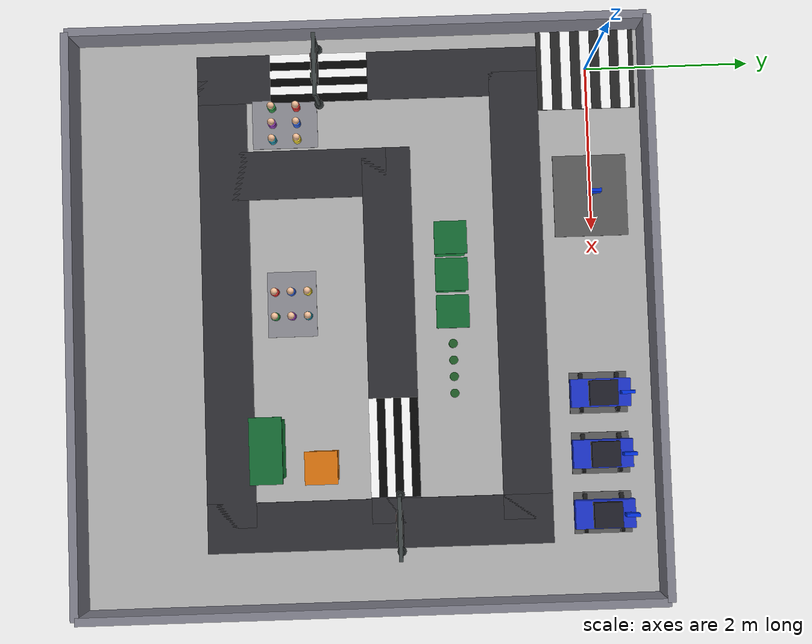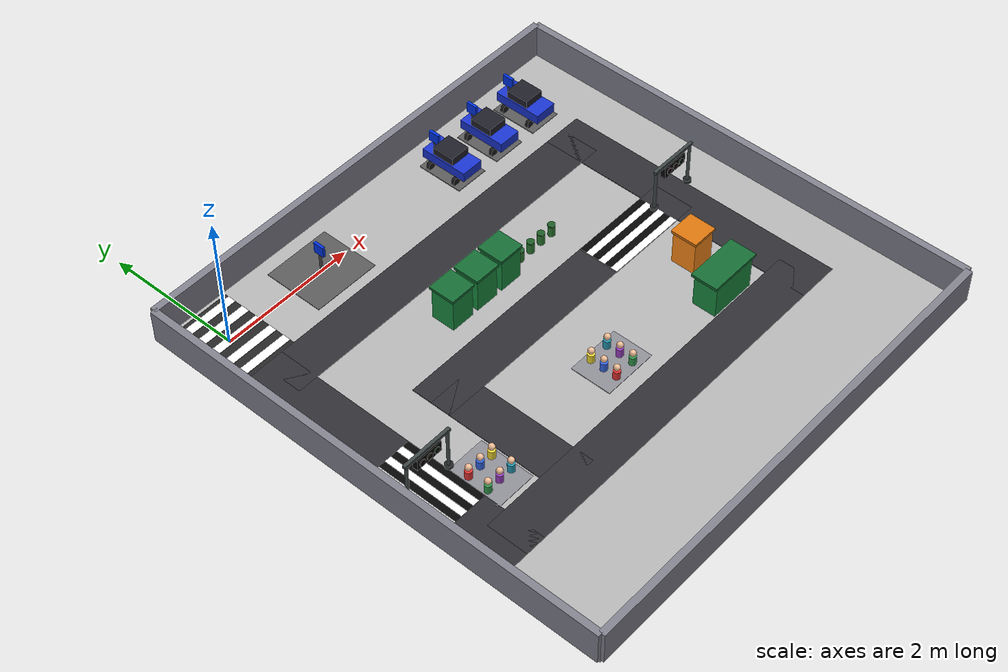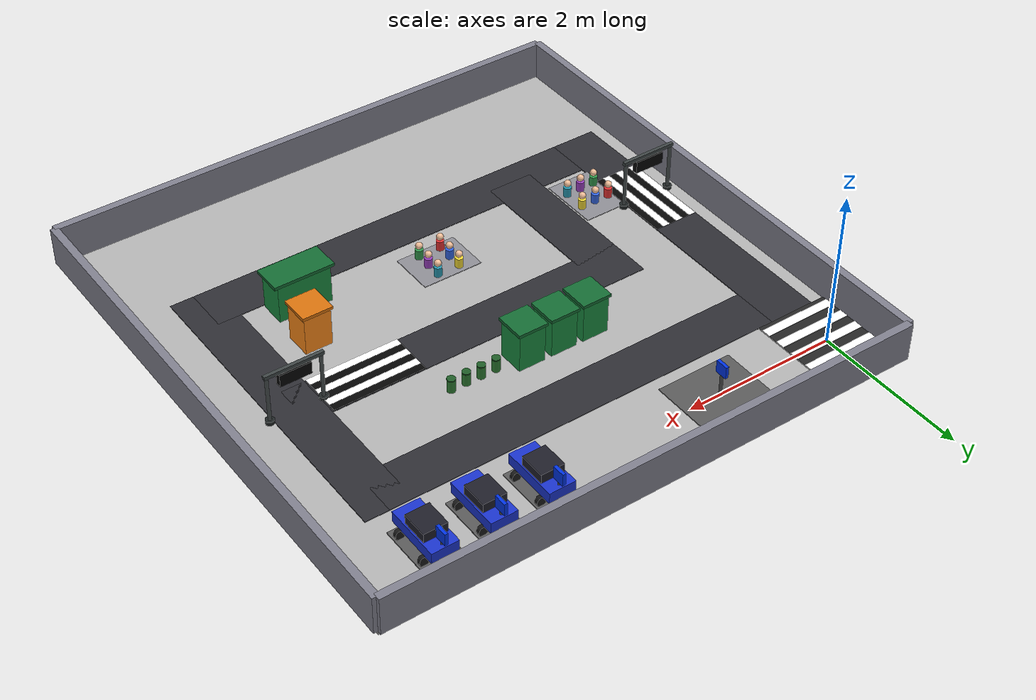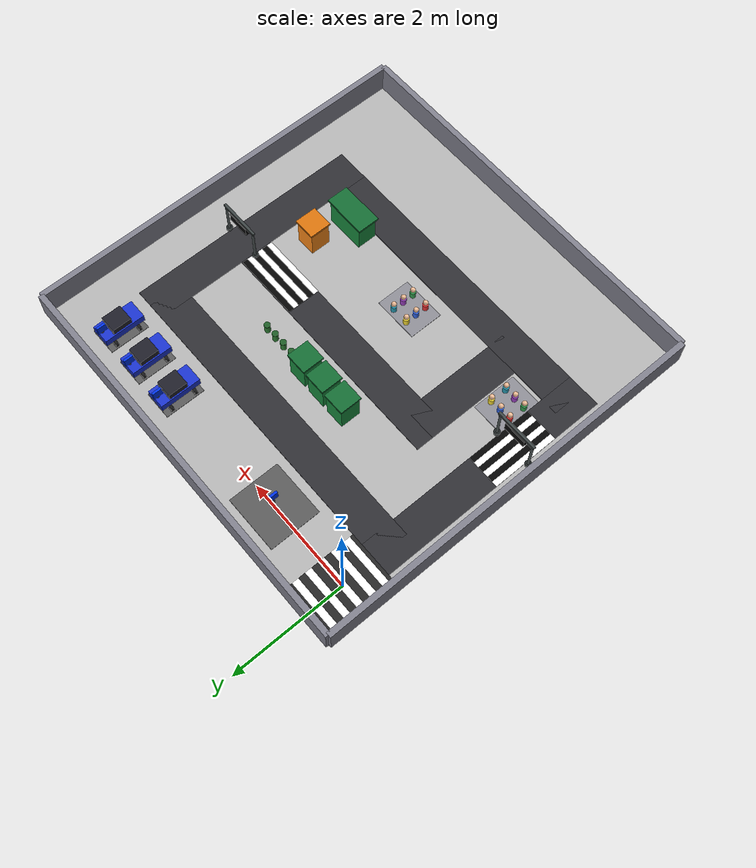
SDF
<sdf version="1.7">
 <world name="robot_nav_field">
  <physics type="ode">
   <max_step_size>0.001</max_step_size>
   <real_time_factor>1</real_time_factor>
   <real_time_update_rate>1000</real_time_update_rate>
  </physics>
  <scene><ambient>0.45 0.45 0.45 1</ambient><background>0.7 0.7 0.7 1</background><shadows>1</shadows></scene>
  <light name="sun" type="directional">
   <pose>0 0 10 0 -0 0</pose>
   <diffuse>0.8 0.8 0.8 1</diffuse>
   <specular>0.1 0.1 0.1 1</specular>
   <direction>0.3 0.3 -1</direction>
   <attenuation><range>10</range></attenuation>
   <spot><inner_angle>0</inner_angle><outer_angle>0</outer_angle><falloff>0</falloff></spot>
  </light>
  <plugin name="traffic_light_controller" filename="libtraffic_light_plugin.so">
   <red>10</red>
   <green>15</green>
   <yellow>5</yellow>
   <group>traffic_light_top</group>
   <group>traffic_light_bottom</group>
  </plugin>
  <model name="traffic_light_top">
   <static>1</static>
   <link name="gantry">
    <collision name="left_post_collision">
     <pose>-0.34 0 0.32 0 -0 0</pose>
     <geometry><cylinder><radius>0.022</radius><length>0.64</length></cylinder></geometry>
    </collision>
    <collision name="right_post_collision">
     <pose>0.34 0 0.32 0 -0 0</pose>
     <geometry><cylinder><radius>0.022</radius><length>0.64</length></cylinder></geometry>
    </collision>
    <collision name="crossbar_collision">
     <pose>0 0 0.66 0 -0 0</pose>
     <geometry><box><size>0.75 0.045 0.045</size></box></geometry>
    </collision>
    <collision name="housing_collision">
     <pose>0 0 0.55 0 -0 0</pose>
     <geometry><box><size>0.4 0.075 0.16</size></box></geometry>
    </collision>
    <visual name="left_foot">
     <pose>-0.34 0 0.025 0 -0 0</pose>
     <geometry><cylinder><radius>0.055</radius><length>0.05</length></cylinder></geometry>
     <material><ambient>0.06 0.07 0.07 1</ambient><diffuse>0.12 0.14 0.14 1</diffuse></material>
    </visual>
    <visual name="right_foot">
     <pose>0.34 0 0.025 0 -0 0</pose>
     <geometry><cylinder><radius>0.055</radius><length>0.05</length></cylinder></geometry>
     <material><ambient>0.06 0.07 0.07 1</ambient><diffuse>0.12 0.14 0.14 1</diffuse></material>
    </visual>
    <visual name="left_post">
     <pose>-0.34 0 0.32 0 -0 0</pose>
     <geometry><cylinder><radius>0.022</radius><length>0.64</length></cylinder></geometry>
     <material>
      <ambient>0.16 0.18 0.18 1</ambient>
      <diffuse>0.28 0.31 0.31 1</diffuse>
      <specular>0.25 0.25 0.25 1</specular>
     </material>
    </visual>
    <visual name="right_post">
     <pose>0.34 0 0.32 0 -0 0</pose>
     <geometry><cylinder><radius>0.022</radius><length>0.64</length></cylinder></geometry>
     <material>
      <ambient>0.16 0.18 0.18 1</ambient>
      <diffuse>0.28 0.31 0.31 1</diffuse>
      <specular>0.25 0.25 0.25 1</specular>
     </material>
    </visual>
    <visual name="crossbar">
     <pose>0 0 0.66 0 -0 0</pose>
     <geometry><box><size>0.75 0.045 0.045</size></box></geometry>
     <material>
      <ambient>0.12 0.14 0.14 1</ambient>
      <diffuse>0.24 0.27 0.27 1</diffuse>
      <specular>0.25 0.25 0.25 1</specular>
     </material>
    </visual>
    <visual name="left_hanger">
     <pose>-0.14 0 0.615 0 -0 0</pose>
     <geometry><box><size>0.025 0.035 0.07</size></box></geometry>
     <material><ambient>0.06 0.07 0.07 1</ambient><diffuse>0.12 0.14 0.14 1</diffuse></material>
    </visual>
    <visual name="right_hanger">
     <pose>0.14 0 0.615 0 -0 0</pose>
     <geometry><box><size>0.025 0.035 0.07</size></box></geometry>
     <material><ambient>0.06 0.07 0.07 1</ambient><diffuse>0.12 0.14 0.14 1</diffuse></material>
    </visual>
    <visual name="housing">
     <pose>0 0 0.55 0 -0 0</pose>
     <geometry><box><size>0.4 0.075 0.16</size></box></geometry>
     <material>
      <ambient>0.008 0.01 0.01 1</ambient>
      <diffuse>0.016 0.02 0.02 1</diffuse>
      <specular>0.1 0.1 0.1 1</specular>
     </material>
    </visual>
    <visual name="red_lens_off">
     <pose>-0.12 -0.044 0.55 1.5708 -0 0</pose>
     <geometry><cylinder><radius>0.045</radius><length>0.014</length></cylinder></geometry>
     <material><ambient>0.03 0.001 0.001 1</ambient><diffuse>0.045 0.002 0.002 1</diffuse></material>
    </visual>
    <visual name="yellow_lens_off">
     <pose>0 -0.044 0.55 1.5708 -0 0</pose>
     <geometry><cylinder><radius>0.045</radius><length>0.014</length></cylinder></geometry>
     <material><ambient>0.025 0.015 0.001 1</ambient><diffuse>0.04 0.024 0.002 1</diffuse></material>
    </visual>
    <visual name="green_lens_off">
     <pose>0.12 -0.044 0.55 1.5708 -0 0</pose>
     <geometry><cylinder><radius>0.045</radius><length>0.014</length></cylinder></geometry>
     <material><ambient>0.001 0.03 0.003 1</ambient><diffuse>0.002 0.045 0.004 1</diffuse></material>
    </visual>
   </link>
   <pose>0 -3.3 0 0 -0 0</pose>
  </model>
  <model name="traffic_light_top_red_lens">
   <static>1</static>
   <link name="gantry">
    <collision name="left_post_collision">
     <pose>-0.34 0 0.32 0 -0 0</pose>
     <geometry><cylinder><radius>0.022</radius><length>0.64</length></cylinder></geometry>
    </collision>
    <collision name="right_post_collision">
     <pose>0.34 0 0.32 0 -0 0</pose>
     <geometry><cylinder><radius>0.022</radius><length>0.64</length></cylinder></geometry>
    </collision>
    <collision name="crossbar_collision">
     <pose>0 0 0.66 0 -0 0</pose>
     <geometry><box><size>0.75 0.045 0.045</size></box></geometry>
    </collision>
    <collision name="housing_collision">
     <pose>0 0 0.55 0 -0 0</pose>
     <geometry><box><size>0.4 0.075 0.16</size></box></geometry>
    </collision>
    <visual name="left_foot">
     <pose>-0.34 0 0.025 0 -0 0</pose>
     <geometry><cylinder><radius>0.055</radius><length>0.05</length></cylinder></geometry>
     <material><ambient>0.06 0.07 0.07 1</ambient><diffuse>0.12 0.14 0.14 1</diffuse></material>
    </visual>
    <visual name="right_foot">
     <pose>0.34 0 0.025 0 -0 0</pose>
     <geometry><cylinder><radius>0.055</radius><length>0.05</length></cylinder></geometry>
     <material><ambient>0.06 0.07 0.07 1</ambient><diffuse>0.12 0.14 0.14 1</diffuse></material>
    </visual>
    <visual name="left_post">
     <pose>-0.34 0 0.32 0 -0 0</pose>
     <geometry><cylinder><radius>0.022</radius><length>0.64</length></cylinder></geometry>
     <material>
      <ambient>0.16 0.18 0.18 1</ambient>
      <diffuse>0.28 0.31 0.31 1</diffuse>
      <specular>0.25 0.25 0.25 1</specular>
     </material>
    </visual>
    <visual name="right_post">
     <pose>0.34 0 0.32 0 -0 0</pose>
     <geometry><cylinder><radius>0.022</radius><length>0.64</length></cylinder></geometry>
     <material>
      <ambient>0.16 0.18 0.18 1</ambient>
      <diffuse>0.28 0.31 0.31 1</diffuse>
      <specular>0.25 0.25 0.25 1</specular>
     </material>
    </visual>
    <visual name="crossbar">
     <pose>0 0 0.66 0 -0 0</pose>
     <geometry><box><size>0.75 0.045 0.045</size></box></geometry>
     <material>
      <ambient>0.12 0.14 0.14 1</ambient>
      <diffuse>0.24 0.27 0.27 1</diffuse>
      <specular>0.25 0.25 0.25 1</specular>
     </material>
    </visual>
    <visual name="left_hanger">
     <pose>-0.14 0 0.615 0 -0 0</pose>
     <geometry><box><size>0.025 0.035 0.07</size></box></geometry>
     <material><ambient>0.06 0.07 0.07 1</ambient><diffuse>0.12 0.14 0.14 1</diffuse></material>
    </visual>
    <visual name="right_hanger">
     <pose>0.14 0 0.615 0 -0 0</pose>
     <geometry><box><size>0.025 0.035 0.07</size></box></geometry>
     <material><ambient>0.06 0.07 0.07 1</ambient><diffuse>0.12 0.14 0.14 1</diffuse></material>
    </visual>
    <visual name="housing">
     <pose>0 0 0.55 0 -0 0</pose>
     <geometry><box><size>0.4 0.075 0.16</size></box></geometry>
     <material>
      <ambient>0.008 0.01 0.01 1</ambient>
      <diffuse>0.016 0.02 0.02 1</diffuse>
      <specular>0.1 0.1 0.1 1</specular>
     </material>
    </visual>
    <visual name="red_lens_off">
     <pose>-0.12 -0.044 0.55 1.5708 -0 0</pose>
     <geometry><cylinder><radius>0.045</radius><length>0.014</length></cylinder></geometry>
     <material><ambient>0.03 0.001 0.001 1</ambient><diffuse>0.045 0.002 0.002 1</diffuse></material>
    </visual>
    <visual name="yellow_lens_off">
     <pose>0 -0.044 0.55 1.5708 -0 0</pose>
     <geometry><cylinder><radius>0.045</radius><length>0.014</length></cylinder></geometry>
     <material><ambient>0.025 0.015 0.001 1</ambient><diffuse>0.04 0.024 0.002 1</diffuse></material>
    </visual>
    <visual name="green_lens_off">
     <pose>0.12 -0.044 0.55 1.5708 -0 0</pose>
     <geometry><cylinder><radius>0.045</radius><length>0.014</length></cylinder></geometry>
     <material><ambient>0.001 0.03 0.003 1</ambient><diffuse>0.002 0.045 0.004 1</diffuse></material>
    </visual>
   </link>
   <pose>0 -3.3 0 0 -0 0</pose>
  </model>
  <model name="traffic_light_top_yellow_lens">
   <static>1</static>
   <link name="gantry">
    <collision name="left_post_collision">
     <pose>-0.34 0 0.32 0 -0 0</pose>
     <geometry><cylinder><radius>0.022</radius><length>0.64</length></cylinder></geometry>
    </collision>
    <collision name="right_post_collision">
     <pose>0.34 0 0.32 0 -0 0</pose>
     <geometry><cylinder><radius>0.022</radius><length>0.64</length></cylinder></geometry>
    </collision>
    <collision name="crossbar_collision">
     <pose>0 0 0.66 0 -0 0</pose>
     <geometry><box><size>0.75 0.045 0.045</size></box></geometry>
    </collision>
    <collision name="housing_collision">
     <pose>0 0 0.55 0 -0 0</pose>
     <geometry><box><size>0.4 0.075 0.16</size></box></geometry>
    </collision>
    <visual name="left_foot">
     <pose>-0.34 0 0.025 0 -0 0</pose>
     <geometry><cylinder><radius>0.055</radius><length>0.05</length></cylinder></geometry>
     <material><ambient>0.06 0.07 0.07 1</ambient><diffuse>0.12 0.14 0.14 1</diffuse></material>
    </visual>
    <visual name="right_foot">
     <pose>0.34 0 0.025 0 -0 0</pose>
     <geometry><cylinder><radius>0.055</radius><length>0.05</length></cylinder></geometry>
     <material><ambient>0.06 0.07 0.07 1</ambient><diffuse>0.12 0.14 0.14 1</diffuse></material>
    </visual>
    <visual name="left_post">
     <pose>-0.34 0 0.32 0 -0 0</pose>
     <geometry><cylinder><radius>0.022</radius><length>0.64</length></cylinder></geometry>
     <material>
      <ambient>0.16 0.18 0.18 1</ambient>
      <diffuse>0.28 0.31 0.31 1</diffuse>
      <specular>0.25 0.25 0.25 1</specular>
     </material>
    </visual>
    <visual name="right_post">
     <pose>0.34 0 0.32 0 -0 0</pose>
     <geometry><cylinder><radius>0.022</radius><length>0.64</length></cylinder></geometry>
     <material>
      <ambient>0.16 0.18 0.18 1</ambient>
      <diffuse>0.28 0.31 0.31 1</diffuse>
      <specular>0.25 0.25 0.25 1</specular>
     </material>
    </visual>
    <visual name="crossbar">
     <pose>0 0 0.66 0 -0 0</pose>
     <geometry><box><size>0.75 0.045 0.045</size></box></geometry>
     <material>
      <ambient>0.12 0.14 0.14 1</ambient>
      <diffuse>0.24 0.27 0.27 1</diffuse>
      <specular>0.25 0.25 0.25 1</specular>
     </material>
    </visual>
    <visual name="left_hanger">
     <pose>-0.14 0 0.615 0 -0 0</pose>
     <geometry><box><size>0.025 0.035 0.07</size></box></geometry>
     <material><ambient>0.06 0.07 0.07 1</ambient><diffuse>0.12 0.14 0.14 1</diffuse></material>
    </visual>
    <visual name="right_hanger">
     <pose>0.14 0 0.615 0 -0 0</pose>
     <geometry><box><size>0.025 0.035 0.07</size></box></geometry>
     <material><ambient>0.06 0.07 0.07 1</ambient><diffuse>0.12 0.14 0.14 1</diffuse></material>
    </visual>
    <visual name="housing">
     <pose>0 0 0.55 0 -0 0</pose>
     <geometry><box><size>0.4 0.075 0.16</size></box></geometry>
     <material>
      <ambient>0.008 0.01 0.01 1</ambient>
      <diffuse>0.016 0.02 0.02 1</diffuse>
      <specular>0.1 0.1 0.1 1</specular>
     </material>
    </visual>
    <visual name="red_lens_off">
     <pose>-0.12 -0.044 0.55 1.5708 -0 0</pose>
     <geometry><cylinder><radius>0.045</radius><length>0.014</length></cylinder></geometry>
     <material><ambient>0.03 0.001 0.001 1</ambient><diffuse>0.045 0.002 0.002 1</diffuse></material>
    </visual>
    <visual name="yellow_lens_off">
     <pose>0 -0.044 0.55 1.5708 -0 0</pose>
     <geometry><cylinder><radius>0.045</radius><length>0.014</length></cylinder></geometry>
     <material><ambient>0.025 0.015 0.001 1</ambient><diffuse>0.04 0.024 0.002 1</diffuse></material>
    </visual>
    <visual name="green_lens_off">
     <pose>0.12 -0.044 0.55 1.5708 -0 0</pose>
     <geometry><cylinder><radius>0.045</radius><length>0.014</length></cylinder></geometry>
     <material><ambient>0.001 0.03 0.003 1</ambient><diffuse>0.002 0.045 0.004 1</diffuse></material>
    </visual>
   </link>
   <pose>0 -3.3 0 0 -0 0</pose>
  </model>
  <model name="traffic_light_top_green_lens">
   <static>1</static>
   <link name="gantry">
    <collision name="left_post_collision">
     <pose>-0.34 0 0.32 0 -0 0</pose>
     <geometry><cylinder><radius>0.022</radius><length>0.64</length></cylinder></geometry>
    </collision>
    <collision name="right_post_collision">
     <pose>0.34 0 0.32 0 -0 0</pose>
     <geometry><cylinder><radius>0.022</radius><length>0.64</length></cylinder></geometry>
    </collision>
    <collision name="crossbar_collision">
     <pose>0 0 0.66 0 -0 0</pose>
     <geometry><box><size>0.75 0.045 0.045</size></box></geometry>
    </collision>
    <collision name="housing_collision">
     <pose>0 0 0.55 0 -0 0</pose>
     <geometry><box><size>0.4 0.075 0.16</size></box></geometry>
    </collision>
    <visual name="left_foot">
     <pose>-0.34 0 0.025 0 -0 0</pose>
     <geometry><cylinder><radius>0.055</radius><length>0.05</length></cylinder></geometry>
     <material><ambient>0.06 0.07 0.07 1</ambient><diffuse>0.12 0.14 0.14 1</diffuse></material>
    </visual>
    <visual name="right_foot">
     <pose>0.34 0 0.025 0 -0 0</pose>
     <geometry><cylinder><radius>0.055</radius><length>0.05</length></cylinder></geometry>
     <material><ambient>0.06 0.07 0.07 1</ambient><diffuse>0.12 0.14 0.14 1</diffuse></material>
    </visual>
    <visual name="left_post">
     <pose>-0.34 0 0.32 0 -0 0</pose>
     <geometry><cylinder><radius>0.022</radius><length>0.64</length></cylinder></geometry>
     <material>
      <ambient>0.16 0.18 0.18 1</ambient>
      <diffuse>0.28 0.31 0.31 1</diffuse>
      <specular>0.25 0.25 0.25 1</specular>
     </material>
    </visual>
    <visual name="right_post">
     <pose>0.34 0 0.32 0 -0 0</pose>
     <geometry><cylinder><radius>0.022</radius><length>0.64</length></cylinder></geometry>
     <material>
      <ambient>0.16 0.18 0.18 1</ambient>
      <diffuse>0.28 0.31 0.31 1</diffuse>
      <specular>0.25 0.25 0.25 1</specular>
     </material>
    </visual>
    <visual name="crossbar">
     <pose>0 0 0.66 0 -0 0</pose>
     <geometry><box><size>0.75 0.045 0.045</size></box></geometry>
     <material>
      <ambient>0.12 0.14 0.14 1</ambient>
      <diffuse>0.24 0.27 0.27 1</diffuse>
      <specular>0.25 0.25 0.25 1</specular>
     </material>
    </visual>
    <visual name="left_hanger">
     <pose>-0.14 0 0.615 0 -0 0</pose>
     <geometry><box><size>0.025 0.035 0.07</size></box></geometry>
     <material><ambient>0.06 0.07 0.07 1</ambient><diffuse>0.12 0.14 0.14 1</diffuse></material>
    </visual>
    <visual name="right_hanger">
     <pose>0.14 0 0.615 0 -0 0</pose>
     <geometry><box><size>0.025 0.035 0.07</size></box></geometry>
     <material><ambient>0.06 0.07 0.07 1</ambient><diffuse>0.12 0.14 0.14 1</diffuse></material>
    </visual>
    <visual name="housing">
     <pose>0 0 0.55 0 -0 0</pose>
     <geometry><box><size>0.4 0.075 0.16</size></box></geometry>
     <material>
      <ambient>0.008 0.01 0.01 1</ambient>
      <diffuse>0.016 0.02 0.02 1</diffuse>
      <specular>0.1 0.1 0.1 1</specular>
     </material>
    </visual>
    <visual name="red_lens_off">
     <pose>-0.12 -0.044 0.55 1.5708 -0 0</pose>
     <geometry><cylinder><radius>0.045</radius><length>0.014</length></cylinder></geometry>
     <material><ambient>0.03 0.001 0.001 1</ambient><diffuse>0.045 0.002 0.002 1</diffuse></material>
    </visual>
    <visual name="yellow_lens_off">
     <pose>0 -0.044 0.55 1.5708 -0 0</pose>
     <geometry><cylinder><radius>0.045</radius><length>0.014</length></cylinder></geometry>
     <material><ambient>0.025 0.015 0.001 1</ambient><diffuse>0.04 0.024 0.002 1</diffuse></material>
    </visual>
    <visual name="green_lens_off">
     <pose>0.12 -0.044 0.55 1.5708 -0 0</pose>
     <geometry><cylinder><radius>0.045</radius><length>0.014</length></cylinder></geometry>
     <material><ambient>0.001 0.03 0.003 1</ambient><diffuse>0.002 0.045 0.004 1</diffuse></material>
    </visual>
   </link>
   <pose>0 -3.3 0 0 -0 0</pose>
  </model>
  <model name="traffic_light_bottom">
   <static>1</static>
   <link name="gantry">
    <collision name="left_post_collision">
     <pose>-0.34 0 0.32 0 -0 0</pose>
     <geometry><cylinder><radius>0.022</radius><length>0.64</length></cylinder></geometry>
    </collision>
    <collision name="right_post_collision">
     <pose>0.34 0 0.32 0 -0 0</pose>
     <geometry><cylinder><radius>0.022</radius><length>0.64</length></cylinder></geometry>
    </collision>
    <collision name="crossbar_collision">
     <pose>0 0 0.66 0 -0 0</pose>
     <geometry><box><size>0.75 0.045 0.045</size></box></geometry>
    </collision>
    <collision name="housing_collision">
     <pose>0 0 0.55 0 -0 0</pose>
     <geometry><box><size>0.4 0.075 0.16</size></box></geometry>
    </collision>
    <visual name="left_foot">
     <pose>-0.34 0 0.025 0 -0 0</pose>
     <geometry><cylinder><radius>0.055</radius><length>0.05</length></cylinder></geometry>
     <material><ambient>0.06 0.07 0.07 1</ambient><diffuse>0.12 0.14 0.14 1</diffuse></material>
    </visual>
    <visual name="right_foot">
     <pose>0.34 0 0.025 0 -0 0</pose>
     <geometry><cylinder><radius>0.055</radius><length>0.05</length></cylinder></geometry>
     <material><ambient>0.06 0.07 0.07 1</ambient><diffuse>0.12 0.14 0.14 1</diffuse></material>
    </visual>
    <visual name="left_post">
     <pose>-0.34 0 0.32 0 -0 0</pose>
     <geometry><cylinder><radius>0.022</radius><length>0.64</length></cylinder></geometry>
     <material>
      <ambient>0.16 0.18 0.18 1</ambient>
      <diffuse>0.28 0.31 0.31 1</diffuse>
      <specular>0.25 0.25 0.25 1</specular>
     </material>
    </visual>
    <visual name="right_post">
     <pose>0.34 0 0.32 0 -0 0</pose>
     <geometry><cylinder><radius>0.022</radius><length>0.64</length></cylinder></geometry>
     <material>
      <ambient>0.16 0.18 0.18 1</ambient>
      <diffuse>0.28 0.31 0.31 1</diffuse>
      <specular>0.25 0.25 0.25 1</specular>
     </material>
    </visual>
    <visual name="crossbar">
     <pose>0 0 0.66 0 -0 0</pose>
     <geometry><box><size>0.75 0.045 0.045</size></box></geometry>
     <material>
      <ambient>0.12 0.14 0.14 1</ambient>
      <diffuse>0.24 0.27 0.27 1</diffuse>
      <specular>0.25 0.25 0.25 1</specular>
     </material>
    </visual>
    <visual name="left_hanger">
     <pose>-0.14 0 0.615 0 -0 0</pose>
     <geometry><box><size>0.025 0.035 0.07</size></box></geometry>
     <material><ambient>0.06 0.07 0.07 1</ambient><diffuse>0.12 0.14 0.14 1</diffuse></material>
    </visual>
    <visual name="right_hanger">
     <pose>0.14 0 0.615 0 -0 0</pose>
     <geometry><box><size>0.025 0.035 0.07</size></box></geometry>
     <material><ambient>0.06 0.07 0.07 1</ambient><diffuse>0.12 0.14 0.14 1</diffuse></material>
    </visual>
    <visual name="housing">
     <pose>0 0 0.55 0 -0 0</pose>
     <geometry><box><size>0.4 0.075 0.16</size></box></geometry>
     <material>
      <ambient>0.008 0.01 0.01 1</ambient>
      <diffuse>0.016 0.02 0.02 1</diffuse>
      <specular>0.1 0.1 0.1 1</specular>
     </material>
    </visual>
    <visual name="red_lens_off">
     <pose>-0.12 -0.044 0.55 1.5708 -0 0</pose>
     <geometry><cylinder><radius>0.045</radius><length>0.014</length></cylinder></geometry>
     <material><ambient>0.03 0.001 0.001 1</ambient><diffuse>0.045 0.002 0.002 1</diffuse></material>
    </visual>
    <visual name="yellow_lens_off">
     <pose>0 -0.044 0.55 1.5708 -0 0</pose>
     <geometry><cylinder><radius>0.045</radius><length>0.014</length></cylinder></geometry>
     <material><ambient>0.025 0.015 0.001 1</ambient><diffuse>0.04 0.024 0.002 1</diffuse></material>
    </visual>
    <visual name="green_lens_off">
     <pose>0.12 -0.044 0.55 1.5708 -0 0</pose>
     <geometry><cylinder><radius>0.045</radius><length>0.014</length></cylinder></geometry>
     <material><ambient>0.001 0.03 0.003 1</ambient><diffuse>0.002 0.045 0.004 1</diffuse></material>
    </visual>
   </link>
   <pose>5.5 -2.45 0 0 -0 0</pose>
  </model>
  <model name="traffic_light_bottom_red_lens">
   <static>1</static>
   <link name="gantry">
    <collision name="left_post_collision">
     <pose>-0.34 0 0.32 0 -0 0</pose>
     <geometry><cylinder><radius>0.022</radius><length>0.64</length></cylinder></geometry>
    </collision>
    <collision name="right_post_collision">
     <pose>0.34 0 0.32 0 -0 0</pose>
     <geometry><cylinder><radius>0.022</radius><length>0.64</length></cylinder></geometry>
    </collision>
    <collision name="crossbar_collision">
     <pose>0 0 0.66 0 -0 0</pose>
     <geometry><box><size>0.75 0.045 0.045</size></box></geometry>
    </collision>
    <collision name="housing_collision">
     <pose>0 0 0.55 0 -0 0</pose>
     <geometry><box><size>0.4 0.075 0.16</size></box></geometry>
    </collision>
    <visual name="left_foot">
     <pose>-0.34 0 0.025 0 -0 0</pose>
     <geometry><cylinder><radius>0.055</radius><length>0.05</length></cylinder></geometry>
     <material><ambient>0.06 0.07 0.07 1</ambient><diffuse>0.12 0.14 0.14 1</diffuse></material>
    </visual>
    <visual name="right_foot">
     <pose>0.34 0 0.025 0 -0 0</pose>
     <geometry><cylinder><radius>0.055</radius><length>0.05</length></cylinder></geometry>
     <material><ambient>0.06 0.07 0.07 1</ambient><diffuse>0.12 0.14 0.14 1</diffuse></material>
    </visual>
    <visual name="left_post">
     <pose>-0.34 0 0.32 0 -0 0</pose>
     <geometry><cylinder><radius>0.022</radius><length>0.64</length></cylinder></geometry>
     <material>
      <ambient>0.16 0.18 0.18 1</ambient>
      <diffuse>0.28 0.31 0.31 1</diffuse>
      <specular>0.25 0.25 0.25 1</specular>
     </material>
    </visual>
    <visual name="right_post">
     <pose>0.34 0 0.32 0 -0 0</pose>
     <geometry><cylinder><radius>0.022</radius><length>0.64</length></cylinder></geometry>
     <material>
      <ambient>0.16 0.18 0.18 1</ambient>
      <diffuse>0.28 0.31 0.31 1</diffuse>
      <specular>0.25 0.25 0.25 1</specular>
     </material>
    </visual>
    <visual name="crossbar">
     <pose>0 0 0.66 0 -0 0</pose>
     <geometry><box><size>0.75 0.045 0.045</size></box></geometry>
     <material>
      <ambient>0.12 0.14 0.14 1</ambient>
      <diffuse>0.24 0.27 0.27 1</diffuse>
      <specular>0.25 0.25 0.25 1</specular>
     </material>
    </visual>
    <visual name="left_hanger">
     <pose>-0.14 0 0.615 0 -0 0</pose>
     <geometry><box><size>0.025 0.035 0.07</size></box></geometry>
     <material><ambient>0.06 0.07 0.07 1</ambient><diffuse>0.12 0.14 0.14 1</diffuse></material>
    </visual>
    <visual name="right_hanger">
     <pose>0.14 0 0.615 0 -0 0</pose>
     <geometry><box><size>0.025 0.035 0.07</size></box></geometry>
     <material><ambient>0.06 0.07 0.07 1</ambient><diffuse>0.12 0.14 0.14 1</diffuse></material>
    </visual>
    <visual name="housing">
     <pose>0 0 0.55 0 -0 0</pose>
     <geometry><box><size>0.4 0.075 0.16</size></box></geometry>
     <material>
      <ambient>0.008 0.01 0.01 1</ambient>
      <diffuse>0.016 0.02 0.02 1</diffuse>
      <specular>0.1 0.1 0.1 1</specular>
     </material>
    </visual>
    <visual name="red_lens_off">
     <pose>-0.12 -0.044 0.55 1.5708 -0 0</pose>
     <geometry><cylinder><radius>0.045</radius><length>0.014</length></cylinder></geometry>
     <material><ambient>0.03 0.001 0.001 1</ambient><diffuse>0.045 0.002 0.002 1</diffuse></material>
    </visual>
    <visual name="yellow_lens_off">
     <pose>0 -0.044 0.55 1.5708 -0 0</pose>
     <geometry><cylinder><radius>0.045</radius><length>0.014</length></cylinder></geometry>
     <material><ambient>0.025 0.015 0.001 1</ambient><diffuse>0.04 0.024 0.002 1</diffuse></material>
    </visual>
    <visual name="green_lens_off">
     <pose>0.12 -0.044 0.55 1.5708 -0 0</pose>
     <geometry><cylinder><radius>0.045</radius><length>0.014</length></cylinder></geometry>
     <material><ambient>0.001 0.03 0.003 1</ambient><diffuse>0.002 0.045 0.004 1</diffuse></material>
    </visual>
   </link>
   <pose>5.5 -2.45 0 0 -0 0</pose>
  </model>
  <model name="traffic_light_bottom_yellow_lens">
   <static>1</static>
   <link name="gantry">
    <collision name="left_post_collision">
     <pose>-0.34 0 0.32 0 -0 0</pose>
     <geometry><cylinder><radius>0.022</radius><length>0.64</length></cylinder></geometry>
    </collision>
    <collision name="right_post_collision">
     <pose>0.34 0 0.32 0 -0 0</pose>
     <geometry><cylinder><radius>0.022</radius><length>0.64</length></cylinder></geometry>
    </collision>
    <collision name="crossbar_collision">
     <pose>0 0 0.66 0 -0 0</pose>
     <geometry><box><size>0.75 0.045 0.045</size></box></geometry>
    </collision>
    <collision name="housing_collision">
     <pose>0 0 0.55 0 -0 0</pose>
     <geometry><box><size>0.4 0.075 0.16</size></box></geometry>
    </collision>
    <visual name="left_foot">
     <pose>-0.34 0 0.025 0 -0 0</pose>
     <geometry><cylinder><radius>0.055</radius><length>0.05</length></cylinder></geometry>
     <material><ambient>0.06 0.07 0.07 1</ambient><diffuse>0.12 0.14 0.14 1</diffuse></material>
    </visual>
    <visual name="right_foot">
     <pose>0.34 0 0.025 0 -0 0</pose>
     <geometry><cylinder><radius>0.055</radius><length>0.05</length></cylinder></geometry>
     <material><ambient>0.06 0.07 0.07 1</ambient><diffuse>0.12 0.14 0.14 1</diffuse></material>
    </visual>
    <visual name="left_post">
     <pose>-0.34 0 0.32 0 -0 0</pose>
     <geometry><cylinder><radius>0.022</radius><length>0.64</length></cylinder></geometry>
     <material>
      <ambient>0.16 0.18 0.18 1</ambient>
      <diffuse>0.28 0.31 0.31 1</diffuse>
      <specular>0.25 0.25 0.25 1</specular>
     </material>
    </visual>
    <visual name="right_post">
     <pose>0.34 0 0.32 0 -0 0</pose>
     <geometry><cylinder><radius>0.022</radius><length>0.64</length></cylinder></geometry>
     <material>
      <ambient>0.16 0.18 0.18 1</ambient>
      <diffuse>0.28 0.31 0.31 1</diffuse>
      <specular>0.25 0.25 0.25 1</specular>
     </material>
    </visual>
    <visual name="crossbar">
     <pose>0 0 0.66 0 -0 0</pose>
     <geometry><box><size>0.75 0.045 0.045</size></box></geometry>
     <material>
      <ambient>0.12 0.14 0.14 1</ambient>
      <diffuse>0.24 0.27 0.27 1</diffuse>
      <specular>0.25 0.25 0.25 1</specular>
     </material>
    </visual>
    <visual name="left_hanger">
     <pose>-0.14 0 0.615 0 -0 0</pose>
     <geometry><box><size>0.025 0.035 0.07</size></box></geometry>
     <material><ambient>0.06 0.07 0.07 1</ambient><diffuse>0.12 0.14 0.14 1</diffuse></material>
    </visual>
    <visual name="right_hanger">
     <pose>0.14 0 0.615 0 -0 0</pose>
     <geometry><box><size>0.025 0.035 0.07</size></box></geometry>
     <material><ambient>0.06 0.07 0.07 1</ambient><diffuse>0.12 0.14 0.14 1</diffuse></material>
    </visual>
    <visual name="housing">
     <pose>0 0 0.55 0 -0 0</pose>
     <geometry><box><size>0.4 0.075 0.16</size></box></geometry>
     <material>
      <ambient>0.008 0.01 0.01 1</ambient>
      <diffuse>0.016 0.02 0.02 1</diffuse>
      <specular>0.1 0.1 0.1 1</specular>
     </material>
    </visual>
    <visual name="red_lens_off">
     <pose>-0.12 -0.044 0.55 1.5708 -0 0</pose>
     <geometry><cylinder><radius>0.045</radius><length>0.014</length></cylinder></geometry>
     <material><ambient>0.03 0.001 0.001 1</ambient><diffuse>0.045 0.002 0.002 1</diffuse></material>
    </visual>
    <visual name="yellow_lens_off">
     <pose>0 -0.044 0.55 1.5708 -0 0</pose>
     <geometry><cylinder><radius>0.045</radius><length>0.014</length></cylinder></geometry>
     <material><ambient>0.025 0.015 0.001 1</ambient><diffuse>0.04 0.024 0.002 1</diffuse></material>
    </visual>
    <visual name="green_lens_off">
     <pose>0.12 -0.044 0.55 1.5708 -0 0</pose>
     <geometry><cylinder><radius>0.045</radius><length>0.014</length></cylinder></geometry>
     <material><ambient>0.001 0.03 0.003 1</ambient><diffuse>0.002 0.045 0.004 1</diffuse></material>
    </visual>
   </link>
   <pose>5.5 -2.45 0 0 -0 0</pose>
  </model>
  <model name="traffic_light_bottom_green_lens">
   <static>1</static>
   <link name="gantry">
    <collision name="left_post_collision">
     <pose>-0.34 0 0.32 0 -0 0</pose>
     <geometry><cylinder><radius>0.022</radius><length>0.64</length></cylinder></geometry>
    </collision>
    <collision name="right_post_collision">
     <pose>0.34 0 0.32 0 -0 0</pose>
     <geometry><cylinder><radius>0.022</radius><length>0.64</length></cylinder></geometry>
    </collision>
    <collision name="crossbar_collision">
     <pose>0 0 0.66 0 -0 0</pose>
     <geometry><box><size>0.75 0.045 0.045</size></box></geometry>
    </collision>
    <collision name="housing_collision">
     <pose>0 0 0.55 0 -0 0</pose>
     <geometry><box><size>0.4 0.075 0.16</size></box></geometry>
    </collision>
    <visual name="left_foot">
     <pose>-0.34 0 0.025 0 -0 0</pose>
     <geometry><cylinder><radius>0.055</radius><length>0.05</length></cylinder></geometry>
     <material><ambient>0.06 0.07 0.07 1</ambient><diffuse>0.12 0.14 0.14 1</diffuse></material>
    </visual>
    <visual name="right_foot">
     <pose>0.34 0 0.025 0 -0 0</pose>
     <geometry><cylinder><radius>0.055</radius><length>0.05</length></cylinder></geometry>
     <material><ambient>0.06 0.07 0.07 1</ambient><diffuse>0.12 0.14 0.14 1</diffuse></material>
    </visual>
    <visual name="left_post">
     <pose>-0.34 0 0.32 0 -0 0</pose>
     <geometry><cylinder><radius>0.022</radius><length>0.64</length></cylinder></geometry>
     <material>
      <ambient>0.16 0.18 0.18 1</ambient>
      <diffuse>0.28 0.31 0.31 1</diffuse>
      <specular>0.25 0.25 0.25 1</specular>
     </material>
    </visual>
    <visual name="right_post">
     <pose>0.34 0 0.32 0 -0 0</pose>
     <geometry><cylinder><radius>0.022</radius><length>0.64</length></cylinder></geometry>
     <material>
      <ambient>0.16 0.18 0.18 1</ambient>
      <diffuse>0.28 0.31 0.31 1</diffuse>
      <specular>0.25 0.25 0.25 1</specular>
     </material>
    </visual>
    <visual name="crossbar">
     <pose>0 0 0.66 0 -0 0</pose>
     <geometry><box><size>0.75 0.045 0.045</size></box></geometry>
     <material>
      <ambient>0.12 0.14 0.14 1</ambient>
      <diffuse>0.24 0.27 0.27 1</diffuse>
      <specular>0.25 0.25 0.25 1</specular>
     </material>
    </visual>
    <visual name="left_hanger">
     <pose>-0.14 0 0.615 0 -0 0</pose>
     <geometry><box><size>0.025 0.035 0.07</size></box></geometry>
     <material><ambient>0.06 0.07 0.07 1</ambient><diffuse>0.12 0.14 0.14 1</diffuse></material>
    </visual>
    <visual name="right_hanger">
     <pose>0.14 0 0.615 0 -0 0</pose>
     <geometry><box><size>0.025 0.035 0.07</size></box></geometry>
     <material><ambient>0.06 0.07 0.07 1</ambient><diffuse>0.12 0.14 0.14 1</diffuse></material>
    </visual>
    <visual name="housing">
     <pose>0 0 0.55 0 -0 0</pose>
     <geometry><box><size>0.4 0.075 0.16</size></box></geometry>
     <material>
      <ambient>0.008 0.01 0.01 1</ambient>
      <diffuse>0.016 0.02 0.02 1</diffuse>
      <specular>0.1 0.1 0.1 1</specular>
     </material>
    </visual>
    <visual name="red_lens_off">
     <pose>-0.12 -0.044 0.55 1.5708 -0 0</pose>
     <geometry><cylinder><radius>0.045</radius><length>0.014</length></cylinder></geometry>
     <material><ambient>0.03 0.001 0.001 1</ambient><diffuse>0.045 0.002 0.002 1</diffuse></material>
    </visual>
    <visual name="yellow_lens_off">
     <pose>0 -0.044 0.55 1.5708 -0 0</pose>
     <geometry><cylinder><radius>0.045</radius><length>0.014</length></cylinder></geometry>
     <material><ambient>0.025 0.015 0.001 1</ambient><diffuse>0.04 0.024 0.002 1</diffuse></material>
    </visual>
    <visual name="green_lens_off">
     <pose>0.12 -0.044 0.55 1.5708 -0 0</pose>
     <geometry><cylinder><radius>0.045</radius><length>0.014</length></cylinder></geometry>
     <material><ambient>0.001 0.03 0.003 1</ambient><diffuse>0.002 0.045 0.004 1</diffuse></material>
    </visual>
   </link>
   <pose>5.5 -2.45 0 0 -0 0</pose>
  </model>
  <model name="ground_plane">
   <static>1</static>
   <pose>2.975 -2.8 -0.025 0 -0 0</pose>
   <link name="ground_link">
    <visual name="ground_visual">
     <geometry><box><size>7 7 0.05</size></box></geometry>
     <material><ambient>0.7 0.7 0.7 1</ambient><diffuse>0.7 0.7 0.7 1</diffuse></material>
    </visual>
    <collision name="ground_collision"><geometry><box><size>7 7 0.05</size></box></geometry></collision>
   </link>
  </model>
  <model name="boundary_walls">
   <static>1</static>
   <link name="north_wall">
    <pose>-0.525 -2.8 0.25 0 -0 0</pose>
    <visual name="north_visual">
     <geometry><box><size>0.1 7 0.5</size></box></geometry>
     <material><ambient>0.5 0.5 0.55 1</ambient><diffuse>0.5 0.5 0.55 1</diffuse></material>
    </visual>
    <collision name="north_collision"><geometry><box><size>0.1 7 0.5</size></box></geometry></collision>
   </link>
   <link name="south_wall">
    <pose>6.475 -2.8 0.25 0 -0 0</pose>
    <visual name="south_visual">
     <geometry><box><size>0.1 7 0.5</size></box></geometry>
     <material><ambient>0.5 0.5 0.55 1</ambient><diffuse>0.5 0.5 0.55 1</diffuse></material>
    </visual>
    <collision name="south_collision"><geometry><box><size>0.1 7 0.5</size></box></geometry></collision>
   </link>
   <link name="west_wall">
    <pose>2.975 -6.3 0.25 0 -0 0</pose>
    <visual name="west_visual">
     <geometry><box><size>7 0.1 0.5</size></box></geometry>
     <material><ambient>0.5 0.5 0.55 1</ambient><diffuse>0.5 0.5 0.55 1</diffuse></material>
    </visual>
    <collision name="west_collision"><geometry><box><size>7 0.1 0.5</size></box></geometry></collision>
   </link>
   <link name="east_wall">
    <pose>2.975 0.7 0.25 0 -0 0</pose>
    <visual name="east_visual">
     <geometry><box><size>7 0.1 0.5</size></box></geometry>
     <material><ambient>0.5 0.5 0.55 1</ambient><diffuse>0.5 0.5 0.55 1</diffuse></material>
    </visual>
    <collision name="east_collision"><geometry><box><size>7 0.1 0.5</size></box></geometry></collision>
   </link>
  </model>
  <model name="roads">
   <static>1</static>
   <link name="road_top">
    <pose>0 -2.7 0.005 0 -0 0</pose>
    <visual name="road_top_visual">
     <geometry><box><size>0.6 4.2 0.01</size></box></geometry>
     <material><ambient>0.18 0.18 0.2 1</ambient><diffuse>0.18 0.18 0.2 1</diffuse></material>
    </visual>
    <collision name="road_top_collision"><geometry><box><size>0.6 3.6 0.01</size></box></geometry></collision>
   </link>
   <link name="road_right">
    <pose>2.75 -0.9 0.005 0 -0 0</pose>
    <visual name="road_right_visual">
     <geometry><box><size>5.5 0.6 0.01</size></box></geometry>
     <material><ambient>0.18 0.18 0.2 1</ambient><diffuse>0.18 0.18 0.2 1</diffuse></material>
    </visual>
    <collision name="road_right_collision"><geometry><box><size>5.5 0.6 0.01</size></box></geometry></collision>
   </link>
   <link name="road_bottom_left">
    <pose>5.5 -2.7 0.005 0 -0 0</pose>
    <visual name="road_bl_visual">
     <geometry><box><size>0.6 4.2 0.01</size></box></geometry>
     <material><ambient>0.18 0.18 0.2 1</ambient><diffuse>0.18 0.18 0.2 1</diffuse></material>
    </visual>
    <collision name="road_bl_collision"><geometry><box><size>0.6 3.6 0.01</size></box></geometry></collision>
   </link>
   <link name="road_left">
    <pose>2.75 -4.5 0.005 0 -0 0</pose>
    <visual name="road_left_visual">
     <geometry><box><size>5.5 0.6 0.01</size></box></geometry>
     <material><ambient>0.18 0.18 0.2 1</ambient><diffuse>0.18 0.18 0.2 1</diffuse></material>
    </visual>
    <collision name="road_left_collision"><geometry><box><size>5.5 0.6 0.01</size></box></geometry></collision>
   </link>
   <link name="road_vertical">
    <pose>3.2 -2.5 0.005 0 -0 0</pose>
    <visual name="road_vertical_visual">
     <geometry><box><size>4.6 0.6 0.01</size></box></geometry>
     <material><ambient>0.18 0.18 0.2 1</ambient><diffuse>0.18 0.18 0.2 1</diffuse></material>
    </visual>
    <collision name="road_vertical_collision">
     <geometry><box><size>3.4 0.6 0.01</size></box></geometry>
    </collision>
   </link>
   <link name="road_horizontal">
    <pose>1.2 -3.5 0.005 0 -0 0</pose>
    <visual name="road_horizontal_visual">
     <geometry><box><size>0.6 2 0.01</size></box></geometry>
     <material><ambient>0.18 0.18 0.2 1</ambient><diffuse>0.18 0.18 0.2 1</diffuse></material>
    </visual>
    <collision name="road_horizontal_collision">
     <geometry><box><size>0.6 2 0.01</size></box></geometry>
    </collision>
   </link>
  </model>
  <model name="start_finish">
   <static>1</static>
   <link name="zebra_link">
    <visual name="zebra_base">
     <pose>0 0 0.006 0 -0 0</pose>
     <geometry><box><size>1 1.2 0.012</size></box></geometry>
     <material><ambient>0.15 0.15 0.15 1</ambient><diffuse>0.15 0.15 0.15 1</diffuse></material>
    </visual>
    <collision name="zebra_base_col">
     <pose>0 0 0.006 0 -0 0</pose>
     <geometry><box><size>1 1.2 0.012</size></box></geometry>
    </collision>
    <visual name="stripe_1">
     <pose>0 -0.48 0.013 0 -0 0</pose>
     <geometry><box><size>1 0.12 0.014</size></box></geometry>
     <material><ambient>1 1 1 1</ambient><diffuse>1 1 1 1</diffuse></material>
    </visual>
    <visual name="stripe_2">
     <pose>0 -0.24 0.013 0 -0 0</pose>
     <geometry><box><size>1 0.12 0.014</size></box></geometry>
     <material><ambient>1 1 1 1</ambient><diffuse>1 1 1 1</diffuse></material>
    </visual>
    <visual name="stripe_3">
     <pose>0 0 0.013 0 -0 0</pose>
     <geometry><box><size>1 0.12 0.014</size></box></geometry>
     <material><ambient>1 1 1 1</ambient><diffuse>1 1 1 1</diffuse></material>
    </visual>
    <visual name="stripe_4">
     <pose>0 0.24 0.013 0 -0 0</pose>
     <geometry><box><size>1 0.12 0.014</size></box></geometry>
     <material><ambient>1 1 1 1</ambient><diffuse>1 1 1 1</diffuse></material>
    </visual>
    <visual name="stripe_5">
     <pose>0 0.48 0.013 0 -0 0</pose>
     <geometry><box><size>1 0.12 0.014</size></box></geometry>
     <material><ambient>1 1 1 1</ambient><diffuse>1 1 1 1</diffuse></material>
    </visual>
   </link>
  </model>
  <model name="zebra_top">
   <static>1</static>
   <pose>0 -3.3 -0.006618 0 -0 0</pose>
   <link name="zebra_top_link">
    <visual name="base">
     <pose>0 0 0.006 0 -0 0</pose>
     <geometry><box><size>0.6 1.2 0.012</size></box></geometry>
     <material><ambient>0.2 0.2 0.2 1</ambient><diffuse>0.2 0.2 0.2 1</diffuse></material>
    </visual>
    <collision name="base_col">
     <pose>0 0 0.006 0 -0 0</pose>
     <geometry><box><size>0.6 1.2 0.012</size></box></geometry>
    </collision>
    <visual name="w1">
     <pose>-0.25 0 0.013 0 -0 0</pose>
     <geometry><box><size>0.1 1.2 0.014</size></box></geometry>
     <material><ambient>1 1 1 1</ambient><diffuse>1 1 1 1</diffuse></material>
    </visual>
    <visual name="k1">
     <pose>-0.15 0 0.013 0 -0 0</pose>
     <geometry><box><size>0.1 1.2 0.014</size></box></geometry>
     <material><ambient>0.02 0.02 0.02 1</ambient><diffuse>0.02 0.02 0.02 1</diffuse></material>
    </visual>
    <visual name="w2">
     <pose>-0.05 0 0.013 0 -0 0</pose>
     <geometry><box><size>0.1 1.2 0.014</size></box></geometry>
     <material><ambient>1 1 1 1</ambient><diffuse>1 1 1 1</diffuse></material>
    </visual>
    <visual name="k2">
     <pose>0.05 0 0.013 0 -0 0</pose>
     <geometry><box><size>0.1 1.2 0.014</size></box></geometry>
     <material><ambient>0.02 0.02 0.02 1</ambient><diffuse>0.02 0.02 0.02 1</diffuse></material>
    </visual>
    <visual name="w3">
     <pose>0.15 0 0.013 0 -0 0</pose>
     <geometry><box><size>0.1 1.2 0.014</size></box></geometry>
     <material><ambient>1 1 1 1</ambient><diffuse>1 1 1 1</diffuse></material>
    </visual>
    <visual name="k3">
     <pose>0.25 0 0.013 0 -0 0</pose>
     <geometry><box><size>0.1 1.2 0.014</size></box></geometry>
     <material><ambient>0.02 0.02 0.02 1</ambient><diffuse>0.02 0.02 0.02 1</diffuse></material>
    </visual>
   </link>
  </model>
  <model name="block_a">
   <static>1</static>
   <pose>0.571732 -3.73098 0 0 0 -1.5682</pose>
   <link name="block_a_link">
    <visual name="sidewalk">
     <pose>0 0 0.005 0 -0 0</pose>
     <geometry><box><size>0.8 0.6 0.01</size></box></geometry>
     <material><ambient>0.55 0.55 0.58 1</ambient><diffuse>0.55 0.55 0.58 1</diffuse></material>
    </visual>
    <collision name="sidewalk_col">
     <pose>0 0 0.005 0 -0 0</pose>
     <geometry><box><size>0.8 0.6 0.01</size></box></geometry>
    </collision>
    <visual name="p1_body">
     <pose>-0.15 -0.2 0.07 0 -0 0</pose>
     <geometry><cylinder><radius>0.05</radius><length>0.14</length></cylinder></geometry>
     <material><ambient>0.9 0.2 0.2 1</ambient><diffuse>0.9 0.2 0.2 1</diffuse></material>
    </visual>
    <visual name="p1_head">
     <pose>-0.15 -0.2 0.19 0 -0 0</pose>
     <geometry><sphere><radius>0.045</radius></sphere></geometry>
     <material><ambient>0.95 0.75 0.6 1</ambient><diffuse>0.95 0.75 0.6 1</diffuse></material>
    </visual>
    <visual name="p2_body">
     <pose>-0.15 0 0.07 0 -0 0</pose>
     <geometry><cylinder><radius>0.05</radius><length>0.14</length></cylinder></geometry>
     <material><ambient>0.2 0.4 0.9 1</ambient><diffuse>0.2 0.4 0.9 1</diffuse></material>
    </visual>
    <visual name="p2_head">
     <pose>-0.15 0 0.19 0 -0 0</pose>
     <geometry><sphere><radius>0.045</radius></sphere></geometry>
     <material><ambient>0.95 0.75 0.6 1</ambient><diffuse>0.95 0.75 0.6 1</diffuse></material>
    </visual>
    <visual name="p3_body">
     <pose>-0.15 0.2 0.07 0 -0 0</pose>
     <geometry><cylinder><radius>0.05</radius><length>0.14</length></cylinder></geometry>
     <material><ambient>0.95 0.85 0.2 1</ambient><diffuse>0.95 0.85 0.2 1</diffuse></material>
    </visual>
    <visual name="p3_head">
     <pose>-0.15 0.2 0.19 0 -0 0</pose>
     <geometry><sphere><radius>0.045</radius></sphere></geometry>
     <material><ambient>0.95 0.75 0.6 1</ambient><diffuse>0.95 0.75 0.6 1</diffuse></material>
    </visual>
    <visual name="p4_body">
     <pose>0.15 -0.2 0.07 0 -0 0</pose>
     <geometry><cylinder><radius>0.05</radius><length>0.14</length></cylinder></geometry>
     <material><ambient>0.2 0.6 0.3 1</ambient><diffuse>0.2 0.6 0.3 1</diffuse></material>
    </visual>
    <visual name="p4_head">
     <pose>0.15 -0.2 0.19 0 -0 0</pose>
     <geometry><sphere><radius>0.045</radius></sphere></geometry>
     <material><ambient>0.95 0.75 0.6 1</ambient><diffuse>0.95 0.75 0.6 1</diffuse></material>
    </visual>
    <visual name="p5_body">
     <pose>0.15 0 0.07 0 -0 0</pose>
     <geometry><cylinder><radius>0.05</radius><length>0.14</length></cylinder></geometry>
     <material><ambient>0.6 0.25 0.75 1</ambient><diffuse>0.6 0.25 0.75 1</diffuse></material>
    </visual>
    <visual name="p5_head">
     <pose>0.15 0 0.19 0 -0 0</pose>
     <geometry><sphere><radius>0.045</radius></sphere></geometry>
     <material><ambient>0.95 0.75 0.6 1</ambient><diffuse>0.95 0.75 0.6 1</diffuse></material>
    </visual>
    <visual name="p6_body">
     <pose>0.15 0.2 0.07 0 -0 0</pose>
     <geometry><cylinder><radius>0.05</radius><length>0.14</length></cylinder></geometry>
     <material><ambient>0.15 0.6 0.7 1</ambient><diffuse>0.15 0.6 0.7 1</diffuse></material>
    </visual>
    <visual name="p6_head">
     <pose>0.15 0.2 0.19 0 -0 0</pose>
     <geometry><sphere><radius>0.045</radius></sphere></geometry>
     <material><ambient>0.95 0.75 0.6 1</ambient><diffuse>0.95 0.75 0.6 1</diffuse></material>
    </visual>
   </link>
  </model>
  <model name="block_b">
   <static>1</static>
   <pose>2.8 -3.7 0 0 -0 0</pose>
   <link name="block_b_link">
    <visual name="sidewalk">
     <pose>0 0 0.005 0 -0 0</pose>
     <geometry><box><size>0.8 0.6 0.01</size></box></geometry>
     <material><ambient>0.55 0.55 0.58 1</ambient><diffuse>0.55 0.55 0.58 1</diffuse></material>
    </visual>
    <collision name="sidewalk_col">
     <pose>0 0 0.005 0 -0 0</pose>
     <geometry><box><size>0.8 0.6 0.01</size></box></geometry>
    </collision>
    <visual name="p1_body">
     <pose>-0.15 -0.2 0.07 0 -0 0</pose>
     <geometry><cylinder><radius>0.05</radius><length>0.14</length></cylinder></geometry>
     <material><ambient>0.9 0.2 0.2 1</ambient><diffuse>0.9 0.2 0.2 1</diffuse></material>
    </visual>
    <visual name="p1_head">
     <pose>-0.15 -0.2 0.19 0 -0 0</pose>
     <geometry><sphere><radius>0.045</radius></sphere></geometry>
     <material><ambient>0.95 0.75 0.6 1</ambient><diffuse>0.95 0.75 0.6 1</diffuse></material>
    </visual>
    <visual name="p2_body">
     <pose>-0.15 0 0.07 0 -0 0</pose>
     <geometry><cylinder><radius>0.05</radius><length>0.14</length></cylinder></geometry>
     <material><ambient>0.2 0.4 0.9 1</ambient><diffuse>0.2 0.4 0.9 1</diffuse></material>
    </visual>
    <visual name="p2_head">
     <pose>-0.15 0 0.19 0 -0 0</pose>
     <geometry><sphere><radius>0.045</radius></sphere></geometry>
     <material><ambient>0.95 0.75 0.6 1</ambient><diffuse>0.95 0.75 0.6 1</diffuse></material>
    </visual>
    <visual name="p3_body">
     <pose>-0.15 0.2 0.07 0 -0 0</pose>
     <geometry><cylinder><radius>0.05</radius><length>0.14</length></cylinder></geometry>
     <material><ambient>0.95 0.85 0.2 1</ambient><diffuse>0.95 0.85 0.2 1</diffuse></material>
    </visual>
    <visual name="p3_head">
     <pose>-0.15 0.2 0.19 0 -0 0</pose>
     <geometry><sphere><radius>0.045</radius></sphere></geometry>
     <material><ambient>0.95 0.75 0.6 1</ambient><diffuse>0.95 0.75 0.6 1</diffuse></material>
    </visual>
    <visual name="p4_body">
     <pose>0.15 -0.2 0.07 0 -0 0</pose>
     <geometry><cylinder><radius>0.05</radius><length>0.14</length></cylinder></geometry>
     <material><ambient>0.2 0.6 0.3 1</ambient><diffuse>0.2 0.6 0.3 1</diffuse></material>
    </visual>
    <visual name="p4_head">
     <pose>0.15 -0.2 0.19 0 -0 0</pose>
     <geometry><sphere><radius>0.045</radius></sphere></geometry>
     <material><ambient>0.95 0.75 0.6 1</ambient><diffuse>0.95 0.75 0.6 1</diffuse></material>
    </visual>
    <visual name="p5_body">
     <pose>0.15 0 0.07 0 -0 0</pose>
     <geometry><cylinder><radius>0.05</radius><length>0.14</length></cylinder></geometry>
     <material><ambient>0.6 0.25 0.75 1</ambient><diffuse>0.6 0.25 0.75 1</diffuse></material>
    </visual>
    <visual name="p5_head">
     <pose>0.15 0 0.19 0 -0 0</pose>
     <geometry><sphere><radius>0.045</radius></sphere></geometry>
     <material><ambient>0.95 0.75 0.6 1</ambient><diffuse>0.95 0.75 0.6 1</diffuse></material>
    </visual>
    <visual name="p6_body">
     <pose>0.15 0.2 0.07 0 -0 0</pose>
     <geometry><cylinder><radius>0.05</radius><length>0.14</length></cylinder></geometry>
     <material><ambient>0.15 0.6 0.7 1</ambient><diffuse>0.15 0.6 0.7 1</diffuse></material>
    </visual>
    <visual name="p6_head">
     <pose>0.15 0.2 0.19 0 -0 0</pose>
     <geometry><sphere><radius>0.045</radius></sphere></geometry>
     <material><ambient>0.95 0.75 0.6 1</ambient><diffuse>0.95 0.75 0.6 1</diffuse></material>
    </visual>
   </link>
  </model>
  <model name="building_a">
   <static>1</static>
   <pose>2.1 -1.75 0 0 -0 0</pose>
   <link name="building_a_link">
    <visual name="body">
     <pose>0 0 0.25 0 -0 0</pose>
     <geometry><box><size>0.35 0.35 0.5</size></box></geometry>
     <material><ambient>0.1 0.55 0.25 1</ambient><diffuse>0.1 0.55 0.25 1</diffuse></material>
    </visual>
    <collision name="body_col">
     <pose>0 0 0.25 0 -0 0</pose>
     <geometry><box><size>0.35 0.35 0.5</size></box></geometry>
    </collision>
    <visual name="roof">
     <pose>0 0 0.52 0 -0 0</pose>
     <geometry><box><size>0.39 0.39 0.04</size></box></geometry>
     <material><ambient>0.08 0.42 0.2 1</ambient><diffuse>0.08 0.42 0.2 1</diffuse></material>
    </visual>
   </link>
  </model>
  <model name="building_b">
   <static>1</static>
   <pose>2.54 -1.75 0 0 -0 0</pose>
   <link name="building_b_link">
    <visual name="body">
     <pose>0 0 0.25 0 -0 0</pose>
     <geometry><box><size>0.35 0.35 0.5</size></box></geometry>
     <material><ambient>0.1 0.55 0.25 1</ambient><diffuse>0.1 0.55 0.25 1</diffuse></material>
    </visual>
    <collision name="body_col">
     <pose>0 0 0.25 0 -0 0</pose>
     <geometry><box><size>0.35 0.35 0.5</size></box></geometry>
    </collision>
    <visual name="roof">
     <pose>0 0 0.52 0 -0 0</pose>
     <geometry><box><size>0.39 0.39 0.04</size></box></geometry>
     <material><ambient>0.08 0.42 0.2 1</ambient><diffuse>0.08 0.42 0.2 1</diffuse></material>
    </visual>
   </link>
  </model>
  <model name="building_c">
   <static>1</static>
   <pose>2.98 -1.75 0 0 -0 0</pose>
   <link name="building_c_link">
    <visual name="body">
     <pose>0 0 0.25 0 -0 0</pose>
     <geometry><box><size>0.35 0.35 0.5</size></box></geometry>
     <material><ambient>0.1 0.55 0.25 1</ambient><diffuse>0.1 0.55 0.25 1</diffuse></material>
    </visual>
    <collision name="body_col">
     <pose>0 0 0.25 0 -0 0</pose>
     <geometry><box><size>0.35 0.35 0.5</size></box></geometry>
    </collision>
    <visual name="roof">
     <pose>0 0 0.52 0 -0 0</pose>
     <geometry><box><size>0.39 0.39 0.04</size></box></geometry>
     <material><ambient>0.08 0.42 0.2 1</ambient><diffuse>0.08 0.42 0.2 1</diffuse></material>
    </visual>
   </link>
  </model>
  <model name="ev_parking_zone">
   <static>1</static>
   <pose>1.58 0 0 0 -0 0</pose>
   <link name="ev_parking_link">
    <visual name="pad">
     <pose>0 0 0.005 0 -0 0</pose>
     <geometry><box><size>1 0.9 0.01</size></box></geometry>
     <material><ambient>0.35 0.35 0.35 1</ambient><diffuse>0.35 0.35 0.35 1</diffuse></material>
    </visual>
    <collision name="pad_col">
     <pose>0 0 0.005 0 -0 0</pose>
     <geometry><box><size>1 0.9 0.01</size></box></geometry>
    </collision>
    <visual name="p_pole">
     <pose>0 0 0.175 0 -0 0</pose>
     <geometry><cylinder><radius>0.02</radius><length>0.35</length></cylinder></geometry>
     <material><ambient>0.3 0.3 0.3 1</ambient><diffuse>0.3 0.3 0.3 1</diffuse></material>
    </visual>
    <collision name="p_pole_col">
     <pose>0 0 0.175 0 -0 0</pose>
     <geometry><cylinder><radius>0.02</radius><length>0.35</length></cylinder></geometry>
    </collision>
    <visual name="p_sign">
     <pose>0 0 0.38 0 -0 0</pose>
     <geometry><box><size>0.04 0.16 0.16</size></box></geometry>
     <material><ambient>0 0.2 0.9 1</ambient><diffuse>0 0.2 0.9 1</diffuse></material>
    </visual>
   </link>
  </model>
  <model name="parking_slots">
   <static>1</static>
   <link name="slot_3">
    <pose>4 0 0.006 0 -0 0</pose>
    <visual name="slot3_visual">
     <geometry><box><size>0.5 0.7 0.012</size></box></geometry>
     <material><ambient>0.35 0.35 0.35 1</ambient><diffuse>0.35 0.35 0.35 1</diffuse></material>
    </visual>
    <collision name="slot3_col"><geometry><box><size>0.5 0.7 0.012</size></box></geometry></collision>
   </link>
   <link name="slot_2">
    <pose>4.73 0 0.006 0 -0 0</pose>
    <visual name="slot2_visual">
     <geometry><box><size>0.5 0.7 0.012</size></box></geometry>
     <material><ambient>0.35 0.35 0.35 1</ambient><diffuse>0.35 0.35 0.35 1</diffuse></material>
    </visual>
    <collision name="slot2_col"><geometry><box><size>0.5 0.7 0.012</size></box></geometry></collision>
   </link>
   <link name="slot_1">
    <pose>5.45 0 0.006 0 -0 0</pose>
    <visual name="slot1_visual">
     <geometry><box><size>0.5 0.7 0.012</size></box></geometry>
     <material><ambient>0.35 0.35 0.35 1</ambient><diffuse>0.35 0.35 0.35 1</diffuse></material>
    </visual>
    <collision name="slot1_col"><geometry><box><size>0.5 0.7 0.012</size></box></geometry></collision>
   </link>
  </model>
  <model name="car_slot_3">
   <static>1</static>
   <pose>4 0 0 0 -0 1.5708</pose>
   <link name="car_slot_3_link">
    <visual name="body">
     <pose>0 0 0.19 0 -0 0</pose>
     <geometry><box><size>0.72 0.34 0.14</size></box></geometry>
     <material><ambient>0.1 0.2 0.8 1</ambient><diffuse>0.1 0.2 0.8 1</diffuse></material>
    </visual>
    <collision name="body_col">
     <pose>0 0 0.19 0 -0 0</pose>
     <geometry><box><size>0.72 0.34 0.14</size></box></geometry>
    </collision>
    <visual name="cabin">
     <pose>0.02 0 0.32 0 -0 0</pose>
     <geometry><box><size>0.34 0.3 0.12</size></box></geometry>
     <material><ambient>0.12 0.12 0.16 1</ambient><diffuse>0.12 0.12 0.16 1</diffuse></material>
    </visual>
    <visual name="w1">
     <pose>0.22 0.18 0.06 3.14159 1.57079 3.14159</pose>
     <geometry><cylinder><radius>0.06</radius><length>0.05</length></cylinder></geometry>
     <material><ambient>0.1 0.1 0.1 1</ambient><diffuse>0.1 0.1 0.1 1</diffuse></material>
    </visual>
    <visual name="w2">
     <pose>0.22 -0.18 0.06 3.14159 1.57079 3.14159</pose>
     <geometry><cylinder><radius>0.06</radius><length>0.05</length></cylinder></geometry>
     <material><ambient>0.1 0.1 0.1 1</ambient><diffuse>0.1 0.1 0.1 1</diffuse></material>
    </visual>
    <visual name="w3">
     <pose>-0.22 0.18 0.06 3.14159 1.57079 3.14159</pose>
     <geometry><cylinder><radius>0.06</radius><length>0.05</length></cylinder></geometry>
     <material><ambient>0.1 0.1 0.1 1</ambient><diffuse>0.1 0.1 0.1 1</diffuse></material>
    </visual>
    <visual name="w4">
     <pose>-0.22 -0.18 0.06 3.14159 1.57079 3.14159</pose>
     <geometry><cylinder><radius>0.06</radius><length>0.05</length></cylinder></geometry>
     <material><ambient>0.1 0.1 0.1 1</ambient><diffuse>0.1 0.1 0.1 1</diffuse></material>
    </visual>
   </link>
  </model>
  <model name="car_slot_2">
   <static>1</static>
   <pose>4.73 0 0 0 -0 1.5708</pose>
   <link name="car_slot_2_link">
    <visual name="body">
     <pose>0 0 0.19 0 -0 0</pose>
     <geometry><box><size>0.72 0.34 0.14</size></box></geometry>
     <material><ambient>0.1 0.2 0.8 1</ambient><diffuse>0.1 0.2 0.8 1</diffuse></material>
    </visual>
    <collision name="body_col">
     <pose>0 0 0.19 0 -0 0</pose>
     <geometry><box><size>0.72 0.34 0.14</size></box></geometry>
    </collision>
    <visual name="cabin">
     <pose>0.02 0 0.32 0 -0 0</pose>
     <geometry><box><size>0.34 0.3 0.12</size></box></geometry>
     <material><ambient>0.12 0.12 0.16 1</ambient><diffuse>0.12 0.12 0.16 1</diffuse></material>
    </visual>
    <visual name="w1">
     <pose>0.22 0.18 0.06 3.14159 1.57079 3.14159</pose>
     <geometry><cylinder><radius>0.06</radius><length>0.05</length></cylinder></geometry>
     <material><ambient>0.1 0.1 0.1 1</ambient><diffuse>0.1 0.1 0.1 1</diffuse></material>
    </visual>
    <visual name="w2">
     <pose>0.22 -0.18 0.06 3.14159 1.57079 3.14159</pose>
     <geometry><cylinder><radius>0.06</radius><length>0.05</length></cylinder></geometry>
     <material><ambient>0.1 0.1 0.1 1</ambient><diffuse>0.1 0.1 0.1 1</diffuse></material>
    </visual>
    <visual name="w3">
     <pose>-0.22 0.18 0.06 3.14159 1.57079 3.14159</pose>
     <geometry><cylinder><radius>0.06</radius><length>0.05</length></cylinder></geometry>
     <material><ambient>0.1 0.1 0.1 1</ambient><diffuse>0.1 0.1 0.1 1</diffuse></material>
    </visual>
    <visual name="w4">
     <pose>-0.22 -0.18 0.06 3.14159 1.57079 3.14159</pose>
     <geometry><cylinder><radius>0.06</radius><length>0.05</length></cylinder></geometry>
     <material><ambient>0.1 0.1 0.1 1</ambient><diffuse>0.1 0.1 0.1 1</diffuse></material>
    </visual>
   </link>
  </model>
  <model name="car_slot_1">
   <static>1</static>
   <pose>5.45 0 0 0 -0 1.5708</pose>
   <link name="car_slot_1_link">
    <visual name="body">
     <pose>0 0 0.19 0 -0 0</pose>
     <geometry><box><size>0.72 0.34 0.14</size></box></geometry>
     <material><ambient>0.1 0.2 0.8 1</ambient><diffuse>0.1 0.2 0.8 1</diffuse></material>
    </visual>
    <collision name="body_col">
     <pose>0 0 0.19 0 -0 0</pose>
     <geometry><box><size>0.72 0.34 0.14</size></box></geometry>
    </collision>
    <visual name="cabin">
     <pose>0.02 0 0.32 0 -0 0</pose>
     <geometry><box><size>0.34 0.3 0.12</size></box></geometry>
     <material><ambient>0.12 0.12 0.16 1</ambient><diffuse>0.12 0.12 0.16 1</diffuse></material>
    </visual>
    <visual name="w1">
     <pose>0.22 0.18 0.06 3.14159 1.57079 3.14159</pose>
     <geometry><cylinder><radius>0.06</radius><length>0.05</length></cylinder></geometry>
     <material><ambient>0.1 0.1 0.1 1</ambient><diffuse>0.1 0.1 0.1 1</diffuse></material>
    </visual>
    <visual name="w2">
     <pose>0.22 -0.18 0.06 3.14159 1.57079 3.14159</pose>
     <geometry><cylinder><radius>0.06</radius><length>0.05</length></cylinder></geometry>
     <material><ambient>0.1 0.1 0.1 1</ambient><diffuse>0.1 0.1 0.1 1</diffuse></material>
    </visual>
    <visual name="w3">
     <pose>-0.22 0.18 0.06 3.14159 1.57079 3.14159</pose>
     <geometry><cylinder><radius>0.06</radius><length>0.05</length></cylinder></geometry>
     <material><ambient>0.1 0.1 0.1 1</ambient><diffuse>0.1 0.1 0.1 1</diffuse></material>
    </visual>
    <visual name="w4">
     <pose>-0.22 -0.18 0.06 3.14159 1.57079 3.14159</pose>
     <geometry><cylinder><radius>0.06</radius><length>0.05</length></cylinder></geometry>
     <material><ambient>0.1 0.1 0.1 1</ambient><diffuse>0.1 0.1 0.1 1</diffuse></material>
    </visual>
   </link>
  </model>
  <model name="p_sign_slot_3">
   <static>1</static>
   <pose>4 0.3 0 0 -0 0</pose>
   <link name="ps3_link">
    <visual name="pole">
     <pose>0 0 0.175 0 -0 0</pose>
     <geometry><cylinder><radius>0.02</radius><length>0.35</length></cylinder></geometry>
     <material><ambient>0.3 0.3 0.3 1</ambient><diffuse>0.3 0.3 0.3 1</diffuse></material>
    </visual>
    <collision name="pole_col">
     <pose>0 0 0.175 0 -0 0</pose>
     <geometry><cylinder><radius>0.02</radius><length>0.35</length></cylinder></geometry>
    </collision>
    <visual name="sign">
     <pose>0 0 0.38 0 -0 0</pose>
     <geometry><box><size>0.04 0.16 0.16</size></box></geometry>
     <material><ambient>0 0.2 0.9 1</ambient><diffuse>0 0.2 0.9 1</diffuse></material>
    </visual>
   </link>
  </model>
  <model name="p_sign_slot_2">
   <static>1</static>
   <pose>4.73 0.3 0 0 -0 0</pose>
   <link name="ps2_link">
    <visual name="pole">
     <pose>0 0 0.175 0 -0 0</pose>
     <geometry><cylinder><radius>0.02</radius><length>0.35</length></cylinder></geometry>
     <material><ambient>0.3 0.3 0.3 1</ambient><diffuse>0.3 0.3 0.3 1</diffuse></material>
    </visual>
    <collision name="pole_col">
     <pose>0 0 0.175 0 -0 0</pose>
     <geometry><cylinder><radius>0.02</radius><length>0.35</length></cylinder></geometry>
    </collision>
    <visual name="sign">
     <pose>0 0 0.38 0 -0 0</pose>
     <geometry><box><size>0.04 0.16 0.16</size></box></geometry>
     <material><ambient>0 0.2 0.9 1</ambient><diffuse>0 0.2 0.9 1</diffuse></material>
    </visual>
   </link>
  </model>
  <model name="p_sign_slot_1">
   <static>1</static>
   <pose>5.45 0.3 0 0 -0 0</pose>
   <link name="ps1_link">
    <visual name="pole">
     <pose>0 0 0.175 0 -0 0</pose>
     <geometry><cylinder><radius>0.02</radius><length>0.35</length></cylinder></geometry>
     <material><ambient>0.3 0.3 0.3 1</ambient><diffuse>0.3 0.3 0.3 1</diffuse></material>
    </visual>
    <collision name="pole_col">
     <pose>0 0 0.175 0 -0 0</pose>
     <geometry><cylinder><radius>0.02</radius><length>0.35</length></cylinder></geometry>
    </collision>
    <visual name="sign">
     <pose>0 0 0.38 0 -0 0</pose>
     <geometry><box><size>0.04 0.16 0.16</size></box></geometry>
     <material><ambient>0 0.2 0.9 1</ambient><diffuse>0 0.2 0.9 1</diffuse></material>
    </visual>
   </link>
  </model>
  <model name="trash_bins">
   <static>1</static>
   <link name="bin_1">
    <pose>3.35 -1.75 0 0 -0 0</pose>
    <visual name="body">
     <pose>0 0 0.085 0 -0 0</pose>
     <geometry><cylinder><radius>0.05</radius><length>0.17</length></cylinder></geometry>
     <material><ambient>0.18 0.49 0.2 1</ambient><diffuse>0.18 0.49 0.2 1</diffuse></material>
    </visual>
    <collision name="body_col">
     <pose>0 0 0.085 0 -0 0</pose>
     <geometry><cylinder><radius>0.05</radius><length>0.17</length></cylinder></geometry>
    </collision>
    <visual name="lid">
     <pose>0 0 0.176 0 -0 0</pose>
     <geometry><cylinder><radius>0.053</radius><length>0.013</length></cylinder></geometry>
     <material><ambient>0.12 0.36 0.15 1</ambient><diffuse>0.12 0.36 0.15 1</diffuse></material>
    </visual>
   </link>
   <link name="bin_2">
    <pose>3.55 -1.75 0 0 -0 0</pose>
    <visual name="body">
     <pose>0 0 0.085 0 -0 0</pose>
     <geometry><cylinder><radius>0.05</radius><length>0.17</length></cylinder></geometry>
     <material><ambient>0.18 0.49 0.2 1</ambient><diffuse>0.18 0.49 0.2 1</diffuse></material>
    </visual>
    <collision name="body_col">
     <pose>0 0 0.085 0 -0 0</pose>
     <geometry><cylinder><radius>0.05</radius><length>0.17</length></cylinder></geometry>
    </collision>
    <visual name="lid">
     <pose>0 0 0.176 0 -0 0</pose>
     <geometry><cylinder><radius>0.053</radius><length>0.013</length></cylinder></geometry>
     <material><ambient>0.12 0.36 0.15 1</ambient><diffuse>0.12 0.36 0.15 1</diffuse></material>
    </visual>
   </link>
   <link name="bin_3">
    <pose>3.75 -1.75 0 0 -0 0</pose>
    <visual name="body">
     <pose>0 0 0.085 0 -0 0</pose>
     <geometry><cylinder><radius>0.05</radius><length>0.17</length></cylinder></geometry>
     <material><ambient>0.18 0.49 0.2 1</ambient><diffuse>0.18 0.49 0.2 1</diffuse></material>
    </visual>
    <collision name="body_col">
     <pose>0 0 0.085 0 -0 0</pose>
     <geometry><cylinder><radius>0.05</radius><length>0.17</length></cylinder></geometry>
    </collision>
    <visual name="lid">
     <pose>0 0 0.176 0 -0 0</pose>
     <geometry><cylinder><radius>0.053</radius><length>0.013</length></cylinder></geometry>
     <material><ambient>0.12 0.36 0.15 1</ambient><diffuse>0.12 0.36 0.15 1</diffuse></material>
    </visual>
   </link>
   <link name="bin_4">
    <pose>3.95 -1.75 0 0 -0 0</pose>
    <visual name="body">
     <pose>0 0 0.085 0 -0 0</pose>
     <geometry><cylinder><radius>0.05</radius><length>0.17</length></cylinder></geometry>
     <material><ambient>0.18 0.49 0.2 1</ambient><diffuse>0.18 0.49 0.2 1</diffuse></material>
    </visual>
    <collision name="body_col">
     <pose>0 0 0.085 0 -0 0</pose>
     <geometry><cylinder><radius>0.05</radius><length>0.17</length></cylinder></geometry>
    </collision>
    <visual name="lid">
     <pose>0 0 0.176 0 -0 0</pose>
     <geometry><cylinder><radius>0.053</radius><length>0.013</length></cylinder></geometry>
     <material><ambient>0.12 0.36 0.15 1</ambient><diffuse>0.12 0.36 0.15 1</diffuse></material>
    </visual>
   </link>
  </model>
  <model name="building_d">
   <static>1</static>
   <pose>4.55169 -4.00555 0 0 -0 0</pose>
   <link name="building_d_link">
    <visual name="body">
     <pose>0 0 0.25 0 -0 0</pose>
     <geometry><box><size>0.7 0.35 0.5</size></box></geometry>
     <material><ambient>0.1 0.55 0.25 1</ambient><diffuse>0.1 0.55 0.25 1</diffuse></material>
    </visual>
    <collision name="body_col">
     <pose>0 0 0.25 0 -0 0</pose>
     <geometry><box><size>0.7 0.35 0.5</size></box></geometry>
    </collision>
    <visual name="roof">
     <pose>0 0 0.52 0 -0 0</pose>
     <geometry><box><size>0.79 0.39 0.04</size></box></geometry>
     <material><ambient>0.08 0.42 0.2 1</ambient><diffuse>0.08 0.42 0.2 1</diffuse></material>
    </visual>
   </link>
  </model>
  <model name="station">
   <static>1</static>
   <pose>4.77054 -3.35881 0 0 -0 0</pose>
   <link name="station_link">
    <visual name="body">
     <pose>0 0 0.25 0 -0 0</pose>
     <geometry><box><size>0.35 0.35 0.5</size></box></geometry>
     <material><ambient>1 0.55 0.1 1</ambient><diffuse>1 0.55 0.1 1</diffuse></material>
    </visual>
    <collision name="body_col">
     <pose>0 0 0.25 0 -0 0</pose>
     <geometry><box><size>0.35 0.35 0.5</size></box></geometry>
    </collision>
    <visual name="roof">
     <pose>0 0 0.52 0 -0 0</pose>
     <geometry><box><size>0.39 0.39 0.04</size></box></geometry>
     <material><ambient>0.85 0.45 0.05 1</ambient><diffuse>0.85 0.45 0.05 1</diffuse></material>
    </visual>
   </link>
  </model>
  <model name="zebra_bottom">
   <static>1</static>
   <pose>4.58209 -2.50434 0 0 -0 0</pose>
   <link name="zebra_bottom_link">
    <visual name="base">
     <pose>0 0 0.006 0 -0 0</pose>
     <geometry><box><size>1.2 0.6 0.012</size></box></geometry>
     <material><ambient>0.2 0.2 0.2 1</ambient><diffuse>0.2 0.2 0.2 1</diffuse></material>
    </visual>
    <collision name="base_col">
     <pose>0 0 0.006 0 -0 0</pose>
     <geometry><box><size>1.2 0.6 0.012</size></box></geometry>
    </collision>
    <visual name="w1">
     <pose>0 -0.25 0.013 0 -0 0</pose>
     <geometry><box><size>1.2 0.1 0.014</size></box></geometry>
     <material><ambient>1 1 1 1</ambient><diffuse>1 1 1 1</diffuse></material>
    </visual>
    <visual name="k1">
     <pose>0 -0.15 0.013 0 -0 0</pose>
     <geometry><box><size>1.2 0.1 0.014</size></box></geometry>
     <material><ambient>0.02 0.02 0.02 1</ambient><diffuse>0.02 0.02 0.02 1</diffuse></material>
    </visual>
    <visual name="w2">
     <pose>0 -0.05 0.013 0 -0 0</pose>
     <geometry><box><size>1.2 0.1 0.014</size></box></geometry>
     <material><ambient>1 1 1 1</ambient><diffuse>1 1 1 1</diffuse></material>
    </visual>
    <visual name="k2">
     <pose>0 0.05 0.013 0 -0 0</pose>
     <geometry><box><size>1.2 0.1 0.014</size></box></geometry>
     <material><ambient>0.02 0.02 0.02 1</ambient><diffuse>0.02 0.02 0.02 1</diffuse></material>
    </visual>
    <visual name="w3">
     <pose>0 0.15 0.013 0 -0 0</pose>
     <geometry><box><size>1.2 0.1 0.014</size></box></geometry>
     <material><ambient>1 1 1 1</ambient><diffuse>1 1 1 1</diffuse></material>
    </visual>
    <visual name="k3">
     <pose>0 0.25 0.013 0 -0 0</pose>
     <geometry><box><size>1.2 0.1 0.014</size></box></geometry>
     <material><ambient>0.02 0.02 0.02 1</ambient><diffuse>0.02 0.02 0.02 1</diffuse></material>
    </visual>
   </link>
  </model>
  <gravity>0 0 -9.8</gravity>
  <magnetic_field>6e-06 2.3e-05 -4.2e-05</magnetic_field>
  <atmosphere type="adiabatic"/>
  <spherical_coordinates>
   <surface_model>EARTH_WGS84</surface_model>
   <latitude_deg>0</latitude_deg>
   <longitude_deg>0</longitude_deg>
   <elevation>0</elevation>
   <heading_deg>0</heading_deg>
  </spherical_coordinates>
 </world>
</sdf>
